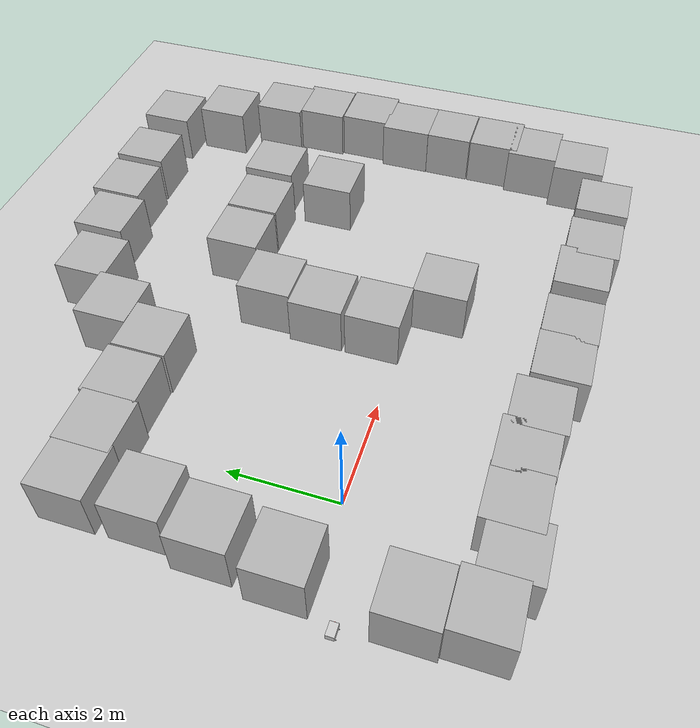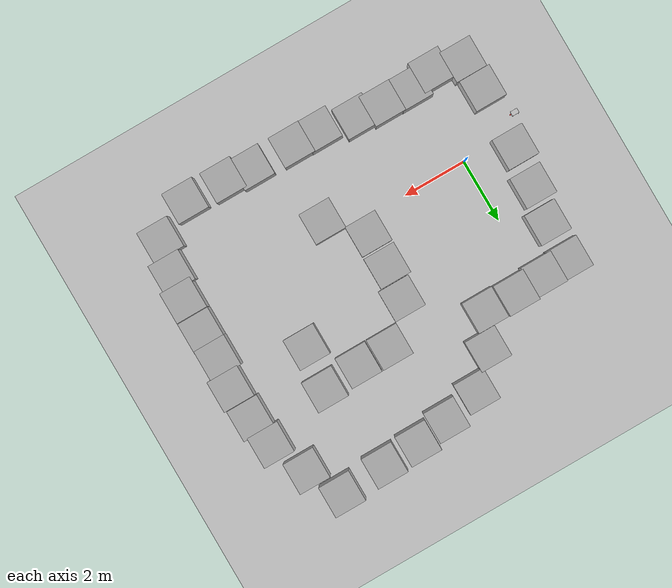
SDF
<?xml version="1.0"?>
<sdf version="1.6">
  <world name="default">

    <plugin
      filename="gz-sim-physics-system"
      name="gz::sim::systems::Physics">
    </plugin>
    <plugin
      filename="gz-sim-user-commands-system"
      name="gz::sim::systems::UserCommands">
    </plugin>
    <plugin
      filename="gz-sim-scene-broadcaster-system"
      name="gz::sim::systems::SceneBroadcaster">
    </plugin>
    <plugin
      filename="gz-sim-sensors-system"
      name="gz::sim::systems::Sensors">
      <render_engine>ogre2</render_engine>
    </plugin>
    <plugin
      filename="gz-sim-imu-system"
      name="gz::sim::systems::Imu">
    </plugin>
    <include>
      <uri>
        https://fuel.gazebosim.org/1.0/OpenRobotics/models/Ground Plane
      </uri>
    </include>

    <include>
      <uri>
        https://fuel.gazebosim.org/1.0/OpenRobotics/models/Sun
      </uri>
    </include>
    <gui fullscreen='0'>
      <camera name='user_camera'>
        <pose frame=''>0.319654 -0.235002 9.29441 0 1.5138 0.009599</pose>
        <view_controller>orbit</view_controller>
        <projection_type>perspective</projection_type>
      </camera>
      <plugin filename="MinimalScene" name="3D View">
        <gz-gui>
          <title>3D View</title>
          <property type="bool" key="showTitleBar">false</property>
          <property type="string" key="state">docked</property>
        </gz-gui>

        <engine>ogre2</engine>
        <scene>scene</scene>
        <ambient_light>0.4 0.4 0.4</ambient_light>
        <background_color>0.8 0.8 0.8</background_color>
        <camera_pose>0.319654 -0.235002 9.29441 0 1.5138 0.009599</camera_pose>
      </plugin>

      <plugin filename="EntityContextMenuPlugin" name="Entity context menu">
        <gz-gui>
          <property key="state" type="string">floating</property>
          <property key="width" type="double">5</property>
          <property key="height" type="double">5</property>
          <property key="showTitleBar" type="bool">false</property>
        </gz-gui>
      </plugin>
      <plugin filename="GzSceneManager" name="Scene Manager">
        <gz-gui>
          <property key="resizable" type="bool">false</property>
          <property key="width" type="double">5</property>
          <property key="height" type="double">5</property>
          <property key="state" type="string">floating</property>
          <property key="showTitleBar" type="bool">false</property>
        </gz-gui>
      </plugin>
      <plugin filename="InteractiveViewControl" name="Interactive view control">
        <gz-gui>
          <property key="resizable" type="bool">false</property>
          <property key="width" type="double">5</property>
          <property key="height" type="double">5</property>
          <property key="state" type="string">floating</property>
          <property key="showTitleBar" type="bool">false</property>
        </gz-gui>
      </plugin>
      <plugin filename="CameraTracking" name="Camera Tracking">
        <gz-gui>
          <property key="resizable" type="bool">false</property>
          <property key="width" type="double">5</property>
          <property key="height" type="double">5</property>
          <property key="state" type="string">floating</property>
          <property key="showTitleBar" type="bool">false</property>
        </gz-gui>
      </plugin>
      <plugin filename="MarkerManager" name="Marker manager">
        <gz-gui>
          <property key="resizable" type="bool">false</property>
          <property key="width" type="double">5</property>
          <property key="height" type="double">5</property>
          <property key="state" type="string">floating</property>
          <property key="showTitleBar" type="bool">false</property>
        </gz-gui>
      </plugin>
      <plugin filename="SelectEntities" name="Select Entities">
        <gz-gui>
          <property key="resizable" type="bool">false</property>
          <property key="width" type="double">5</property>
          <property key="height" type="double">5</property>
          <property key="state" type="string">floating</property>
          <property key="showTitleBar" type="bool">false</property>
        </gz-gui>
      </plugin>

      <plugin filename="Spawn" name="Spawn Entities">
        <gz-gui>
          <property key="resizable" type="bool">false</property>
          <property key="width" type="double">5</property>
          <property key="height" type="double">5</property>
          <property key="state" type="string">floating</property>
          <property key="showTitleBar" type="bool">false</property>
        </gz-gui>
      </plugin>

      <plugin filename="VisualizationCapabilities" name="Visualization Capabilities">
        <gz-gui>
          <property key="resizable" type="bool">false</property>
          <property key="width" type="double">5</property>
          <property key="height" type="double">5</property>
          <property key="state" type="string">floating</property>
          <property key="showTitleBar" type="bool">false</property>
        </gz-gui>
      </plugin>

      <!-- World control -->
      <plugin filename="WorldControl" name="World control">
        <gz-gui>
          <title>World control</title>
          <property type="bool" key="showTitleBar">false</property>
          <property type="bool" key="resizable">false</property>
          <property type="double" key="height">72</property>
          <property type="double" key="z">1</property>

          <property type="string" key="state">floating</property>
          <anchors target="3D View">
            <line own="left" target="left"/>
            <line own="bottom" target="bottom"/>
          </anchors>
        </gz-gui>

        <play_pause>true</play_pause>
        <step>true</step>
        <start_paused>true</start_paused>
        <use_event>true</use_event>

      </plugin>

      <!-- World statistics -->
      <plugin filename="WorldStats" name="World stats">
        <gz-gui>
          <title>World stats</title>
          <property type="bool" key="showTitleBar">false</property>
          <property type="bool" key="resizable">false</property>
          <property type="double" key="height">110</property>
          <property type="double" key="width">290</property>
          <property type="double" key="z">1</property>

          <property type="string" key="state">floating</property>
          <anchors target="3D View">
            <line own="right" target="right"/>
            <line own="bottom" target="bottom"/>
          </anchors>
        </gz-gui>

        <sim_time>true</sim_time>
        <real_time>true</real_time>
        <real_time_factor>true</real_time_factor>
        <iterations>true</iterations>
      </plugin>

      <!-- Insert simple shapes -->
      <plugin filename="Shapes" name="Shapes">
        <gz-gui>
          <property key="resizable" type="bool">false</property>
          <property key="x" type="double">0</property>
          <property key="y" type="double">0</property>
          <property key="width" type="double">250</property>
          <property key="height" type="double">50</property>
          <property key="state" type="string">floating</property>
          <property key="showTitleBar" type="bool">false</property>
          <property key="cardBackground" type="string">#666666</property>
        </gz-gui>
      </plugin>

      <!-- Insert lights -->
      <plugin filename="Lights" name="Lights">
        <gz-gui>
          <property key="resizable" type="bool">false</property>
          <property key="x" type="double">250</property>
          <property key="y" type="double">0</property>
          <property key="width" type="double">150</property>
          <property key="height" type="double">50</property>
          <property key="state" type="string">floating</property>
          <property key="showTitleBar" type="bool">false</property>
          <property key="cardBackground" type="string">#666666</property>
        </gz-gui>
      </plugin>

      <!-- Translate / rotate -->
      <plugin filename="TransformControl" name="Transform control">
        <gz-gui>
          <property key="resizable" type="bool">false</property>
          <property key="x" type="double">0</property>
          <property key="y" type="double">50</property>
          <property key="width" type="double">250</property>
          <property key="height" type="double">50</property>
          <property key="state" type="string">floating</property>
          <property key="showTitleBar" type="bool">false</property>
          <property key="cardBackground" type="string">#777777</property>
        </gz-gui>
      </plugin>

      <!-- Screenshot -->
      <plugin filename="Screenshot" name="Screenshot">
        <gz-gui>
          <property key="resizable" type="bool">false</property>
          <property key="x" type="double">250</property>
          <property key="y" type="double">50</property>
          <property key="width" type="double">50</property>
          <property key="height" type="double">50</property>
          <property key="state" type="string">floating</property>
          <property key="showTitleBar" type="bool">false</property>
          <property key="cardBackground" type="string">#777777</property>
        </gz-gui>
      </plugin>

      <!-- Copy/Paste -->
      <plugin filename="CopyPaste" name="CopyPaste">
        <gz-gui>
          <property key="resizable" type="bool">false</property>
          <property key="x" type="double">300</property>
          <property key="y" type="double">50</property>
          <property key="width" type="double">100</property>
          <property key="height" type="double">50</property>
          <property key="state" type="string">floating</property>
          <property key="showTitleBar" type="bool">false</property>
          <property key="cardBackground" type="string">#777777</property>
        </gz-gui>
      </plugin>

      <!-- Inspector -->
      <plugin filename="ComponentInspector" name="Component inspector">
        <gz-gui>
          <property type="bool" key="showTitleBar">false</property>
          <property type="string" key="state">docked</property>
        </gz-gui>
      </plugin>

      <!-- Entity tree -->
      <plugin filename="EntityTree" name="Entity tree">
        <gz-gui>
          <property type="bool" key="showTitleBar">false</property>
          <property type="string" key="state">docked</property>
        </gz-gui>
      </plugin>
    </gui>

    <physics type="ode">
      <real_time_update_rate>1000.0</real_time_update_rate>
      <max_step_size>0.001</max_step_size>
      <real_time_factor>1</real_time_factor>
      <ode>
        <solver>
          <type>quick</type>
          <iters>150</iters>
          <precon_iters>0</precon_iters>
          <sor>1.400000</sor>
          <use_dynamic_moi_rescaling>1</use_dynamic_moi_rescaling>
        </solver>
        <constraints>
          <cfm>0.00001</cfm>
          <erp>0.2</erp>
          <contact_max_correcting_vel>2000.000000</contact_max_correcting_vel>
          <contact_surface_layer>0.01000</contact_surface_layer>
        </constraints>
      </ode>
    </physics>

    <model name='box'>
      <pose>3.6079806462820692 2.5253344699081568 0.5 0 0 0</pose>
      <link name='box_link'>
        <inertial>
          <inertia>
            <ixx>0.16666</ixx>
            <ixy>0</ixy>
            <ixz>0</ixz>
            <iyy>0.16666</iyy>
            <iyz>0</iyz>
            <izz>0.16666</izz>
          </inertia>
          <mass>1</mass>
          <pose>0 0 0 0 0 0</pose>
        </inertial>
        <collision name='box_collision'>
          <geometry>
            <box>
              <size>1 1 1</size>
            </box>
          </geometry>
          <surface>
            <friction>
              <ode/>
            </friction>
            <bounce/>
            <contact/>
          </surface>
        </collision>
        <visual name='box_visual'>
          <geometry>
            <box>
              <size>1 1 1</size>
            </box>
          </geometry>
          <material>
            <ambient>0.300000012 0.300000012 0.300000012 1</ambient>
            <diffuse>0.699999988 0.699999988 0.699999988 1</diffuse>
            <specular>1 1 1 1</specular>
          </material>
        </visual>
        <pose>0 0 0 0 0 0</pose>
        <enable_wind>false</enable_wind>
      </link>
      <static>false</static>
      <self_collide>false</self_collide>
    </model>
    <model name='box_0'>
      <pose>3.494922661512998 1.4978176082880186 0.5 0 0 0</pose>
      <link name='box_link'>
        <inertial>
          <inertia>
            <ixx>0.16666</ixx>
            <ixy>0</ixy>
            <ixz>0</ixz>
            <iyy>0.16666</iyy>
            <iyz>0</iyz>
            <izz>0.16666</izz>
          </inertia>
          <mass>1</mass>
          <pose>0 0 0 0 0 0</pose>
        </inertial>
        <collision name='box_collision'>
          <geometry>
            <box>
              <size>1 1 1</size>
            </box>
          </geometry>
          <surface>
            <friction>
              <ode/>
            </friction>
            <bounce/>
            <contact/>
          </surface>
        </collision>
        <visual name='box_visual'>
          <geometry>
            <box>
              <size>1 1 1</size>
            </box>
          </geometry>
          <material>
            <ambient>0.300000012 0.300000012 0.300000012 1</ambient>
            <diffuse>0.699999988 0.699999988 0.699999988 1</diffuse>
            <specular>1 1 1 1</specular>
          </material>
        </visual>
        <pose>0 0 0 0 0 0</pose>
        <enable_wind>false</enable_wind>
      </link>
      <static>false</static>
      <self_collide>false</self_collide>
    </model>
    <model name='box_1'>
      <pose>3.4949225119613967 0.43225630653054864 0.5 0 0 0</pose>
      <link name='box_link'>
        <inertial>
          <inertia>
            <ixx>0.16666</ixx>
            <ixy>0</ixy>
            <ixz>0</ixz>
            <iyy>0.16666</iyy>
            <iyz>0</iyz>
            <izz>0.16666</izz>
          </inertia>
          <mass>1</mass>
          <pose>0 0 0 0 0 0</pose>
        </inertial>
        <collision name='box_collision'>
          <geometry>
            <box>
              <size>1 1 1</size>
            </box>
          </geometry>
          <surface>
            <friction>
              <ode/>
            </friction>
            <bounce/>
            <contact/>
          </surface>
        </collision>
        <visual name='box_visual'>
          <geometry>
            <box>
              <size>1 1 1</size>
            </box>
          </geometry>
          <material>
            <ambient>0.300000012 0.300000012 0.300000012 1</ambient>
            <diffuse>0.699999988 0.699999988 0.699999988 1</diffuse>
            <specular>1 1 1 1</specular>
          </material>
        </visual>
        <pose>0 0 0 0 0 0</pose>
        <enable_wind>false</enable_wind>
      </link>
      <static>false</static>
      <self_collide>false</self_collide>
    </model>
    <model name='box_2'>
      <pose>4.4630594434975066 -0.55153767207256765 0.5 0 0 0</pose>
      <link name='box_link'>
        <inertial>
          <inertia>
            <ixx>0.16666</ixx>
            <ixy>0</ixy>
            <ixz>0</ixz>
            <iyy>0.16666</iyy>
            <iyz>0</iyz>
            <izz>0.16666</izz>
          </inertia>
          <mass>1</mass>
          <pose>0 0 0 0 0 0</pose>
        </inertial>
        <collision name='box_collision'>
          <geometry>
            <box>
              <size>1 1 1</size>
            </box>
          </geometry>
          <surface>
            <friction>
              <ode/>
            </friction>
            <bounce/>
            <contact/>
          </surface>
        </collision>
        <visual name='box_visual'>
          <geometry>
            <box>
              <size>1 1 1</size>
            </box>
          </geometry>
          <material>
            <ambient>0.300000012 0.300000012 0.300000012 1</ambient>
            <diffuse>0.699999988 0.699999988 0.699999988 1</diffuse>
            <specular>1 1 1 1</specular>
          </material>
        </visual>
        <pose>0 0 0 0 0 0</pose>
        <enable_wind>false</enable_wind>
      </link>
      <static>false</static>
      <self_collide>false</self_collide>
    </model>
    <model name='box_3'>
      <pose>4.6129606843978133 3.5565113103014911 0.5 0 0 0</pose>
      <link name='box_link'>
        <inertial>
          <inertia>
            <ixx>0.16666</ixx>
            <ixy>0</ixy>
            <ixz>0</ixz>
            <iyy>0.16666</iyy>
            <iyz>0</iyz>
            <izz>0.16666</izz>
          </inertia>
          <mass>1</mass>
          <pose>0 0 0 0 0 0</pose>
        </inertial>
        <collision name='box_collision'>
          <geometry>
            <box>
              <size>1 1 1</size>
            </box>
          </geometry>
          <surface>
            <friction>
              <ode/>
            </friction>
            <bounce/>
            <contact/>
          </surface>
        </collision>
        <visual name='box_visual'>
          <geometry>
            <box>
              <size>1 1 1</size>
            </box>
          </geometry>
          <material>
            <ambient>0.300000012 0.300000012 0.300000012 1</ambient>
            <diffuse>0.699999988 0.699999988 0.699999988 1</diffuse>
            <specular>1 1 1 1</specular>
          </material>
        </visual>
        <pose>0 0 0 0 0 0</pose>
        <enable_wind>false</enable_wind>
      </link>
      <static>false</static>
      <self_collide>false</self_collide>
    </model>
    <model name='box_4'>
      <pose>1.7010573270226828 4.030552841706303 0.5 0 0 0</pose>
      <link name='box_link'>
        <inertial>
          <inertia>
            <ixx>0.16666</ixx>
            <ixy>0</ixy>
            <ixz>0</ixz>
            <iyy>0.16666</iyy>
            <iyz>0</iyz>
            <izz>0.16666</izz>
          </inertia>
          <mass>1</mass>
          <pose>0 0 0 0 0 0</pose>
        </inertial>
        <collision name='box_collision'>
          <geometry>
            <box>
              <size>1 1 1</size>
            </box>
          </geometry>
          <surface>
            <friction>
              <ode/>
            </friction>
            <bounce/>
            <contact/>
          </surface>
        </collision>
        <visual name='box_visual'>
          <geometry>
            <box>
              <size>1 1 1</size>
            </box>
          </geometry>
          <material>
            <ambient>0.300000012 0.300000012 0.300000012 1</ambient>
            <diffuse>0.699999988 0.699999988 0.699999988 1</diffuse>
            <specular>1 1 1 1</specular>
          </material>
        </visual>
        <pose>0 0 0 0 0 0</pose>
        <enable_wind>false</enable_wind>
      </link>
      <static>false</static>
      <self_collide>false</self_collide>
    </model>
    <model name='box_5'>
      <pose>1.2582054842673047 -2.6145004932012856 0.5 0 0 0</pose>
      <link name='box_link'>
        <inertial>
          <inertia>
            <ixx>0.16666</ixx>
            <ixy>0</ixy>
            <ixz>0</ixz>
            <iyy>0.16666</iyy>
            <iyz>0</iyz>
            <izz>0.16666</izz>
          </inertia>
          <mass>1</mass>
          <pose>0 0 0 0 0 0</pose>
        </inertial>
        <collision name='box_collision'>
          <geometry>
            <box>
              <size>1 1 1</size>
            </box>
          </geometry>
          <surface>
            <friction>
              <ode/>
            </friction>
            <bounce/>
            <contact/>
          </surface>
        </collision>
        <visual name='box_visual'>
          <geometry>
            <box>
              <size>1 1 1</size>
            </box>
          </geometry>
          <material>
            <ambient>0.300000012 0.300000012 0.300000012 1</ambient>
            <diffuse>0.699999988 0.699999988 0.699999988 1</diffuse>
            <specular>1 1 1 1</specular>
          </material>
        </visual>
        <pose>0 0 0 0 0 0</pose>
        <enable_wind>false</enable_wind>
      </link>
      <static>false</static>
      <self_collide>false</self_collide>
    </model>
    <model name='box_6'>
      <pose>0.6706154942855127 4.0535003850697073 0.5 0 0 0</pose>
      <link name='box_link'>
        <inertial>
          <inertia>
            <ixx>0.16666</ixx>
            <ixy>0</ixy>
            <ixz>0</ixz>
            <iyy>0.16666</iyy>
            <iyz>0</iyz>
            <izz>0.16666</izz>
          </inertia>
          <mass>1</mass>
          <pose>0 0 0 0 0 0</pose>
        </inertial>
        <collision name='box_collision'>
          <geometry>
            <box>
              <size>1 1 1</size>
            </box>
          </geometry>
          <surface>
            <friction>
              <ode/>
            </friction>
            <bounce/>
            <contact/>
          </surface>
        </collision>
        <visual name='box_visual'>
          <geometry>
            <box>
              <size>1 1 1</size>
            </box>
          </geometry>
          <material>
            <ambient>0.300000012 0.300000012 0.300000012 1</ambient>
            <diffuse>0.699999988 0.699999988 0.699999988 1</diffuse>
            <specular>1 1 1 1</specular>
          </material>
        </visual>
        <pose>0 0 0 0 0 0</pose>
        <enable_wind>false</enable_wind>
      </link>
      <static>false</static>
      <self_collide>false</self_collide>
    </model>
    <model name='box_7'>
      <pose>-0.28243669711069896 3.998690358394934 0.5 0 0 0</pose>
      <link name='box_link'>
        <inertial>
          <inertia>
            <ixx>0.16666</ixx>
            <ixy>0</ixy>
            <ixz>0</ixz>
            <iyy>0.16666</iyy>
            <iyz>0</iyz>
            <izz>0.16666</izz>
          </inertia>
          <mass>1</mass>
          <pose>0 0 0 0 0 0</pose>
        </inertial>
        <collision name='box_collision'>
          <geometry>
            <box>
              <size>1 1 1</size>
            </box>
          </geometry>
          <surface>
            <friction>
              <ode/>
            </friction>
            <bounce/>
            <contact/>
          </surface>
        </collision>
        <visual name='box_visual'>
          <geometry>
            <box>
              <size>1 1 1</size>
            </box>
          </geometry>
          <material>
            <ambient>0.300000012 0.300000012 0.300000012 1</ambient>
            <diffuse>0.699999988 0.699999988 0.699999988 1</diffuse>
            <specular>1 1 1 1</specular>
          </material>
        </visual>
        <pose>0 0 0 0 0 0</pose>
        <enable_wind>false</enable_wind>
      </link>
      <static>false</static>
      <self_collide>false</self_collide>
    </model>
    <model name='box_8'>
      <pose>2.1924004107482391 5.0349059945521963 0.5 0 0 0</pose>
      <link name='box_link'>
        <inertial>
          <inertia>
            <ixx>0.16666</ixx>
            <ixy>0</ixy>
            <ixz>0</ixz>
            <iyy>0.16666</iyy>
            <iyz>0</iyz>
            <izz>0.16666</izz>
          </inertia>
          <mass>1</mass>
          <pose>0 0 0 0 0 0</pose>
        </inertial>
        <collision name='box_collision'>
          <geometry>
            <box>
              <size>1 1 1</size>
            </box>
          </geometry>
          <surface>
            <friction>
              <ode/>
            </friction>
            <bounce/>
            <contact/>
          </surface>
        </collision>
        <visual name='box_visual'>
          <geometry>
            <box>
              <size>1 1 1</size>
            </box>
          </geometry>
          <material>
            <ambient>0.300000012 0.300000012 0.300000012 1</ambient>
            <diffuse>0.699999988 0.699999988 0.699999988 1</diffuse>
            <specular>1 1 1 1</specular>
          </material>
        </visual>
        <pose>0 0 0 0 0 0</pose>
        <enable_wind>false</enable_wind>
      </link>
      <static>false</static>
      <self_collide>false</self_collide>
    </model>
    <model name='box_9'>
      <pose>3.0943881696765345 5.935421168770171 0.5 0 0 0</pose>
      <link name='box_link'>
        <inertial>
          <inertia>
            <ixx>0.16666</ixx>
            <ixy>0</ixy>
            <ixz>0</ixz>
            <iyy>0.16666</iyy>
            <iyz>0</iyz>
            <izz>0.16666</izz>
          </inertia>
          <mass>1</mass>
          <pose>0 0 0 0 0 0</pose>
        </inertial>
        <collision name='box_collision'>
          <geometry>
            <box>
              <size>1 1 1</size>
            </box>
          </geometry>
          <surface>
            <friction>
              <ode/>
            </friction>
            <bounce/>
            <contact/>
          </surface>
        </collision>
        <visual name='box_visual'>
          <geometry>
            <box>
              <size>1 1 1</size>
            </box>
          </geometry>
          <material>
            <ambient>0.300000012 0.300000012 0.300000012 1</ambient>
            <diffuse>0.699999988 0.699999988 0.699999988 1</diffuse>
            <specular>1 1 1 1</specular>
          </material>
        </visual>
        <pose>0 0 0 0 0 0</pose>
        <enable_wind>false</enable_wind>
      </link>
      <static>false</static>
      <self_collide>false</self_collide>
    </model>
    <model name='box_10'>
      <pose>4.2585700037728076 6.2045571536851858 0.5 0 0 0</pose>
      <link name='box_link'>
        <inertial>
          <inertia>
            <ixx>0.16666</ixx>
            <ixy>0</ixy>
            <ixz>0</ixz>
            <iyy>0.16666</iyy>
            <iyz>0</iyz>
            <izz>0.16666</izz>
          </inertia>
          <mass>1</mass>
          <pose>0 0 0 0 0 0</pose>
        </inertial>
        <collision name='box_collision'>
          <geometry>
            <box>
              <size>1 1 1</size>
            </box>
          </geometry>
          <surface>
            <friction>
              <ode/>
            </friction>
            <bounce/>
            <contact/>
          </surface>
        </collision>
        <visual name='box_visual'>
          <geometry>
            <box>
              <size>1 1 1</size>
            </box>
          </geometry>
          <material>
            <ambient>0.300000012 0.300000012 0.300000012 1</ambient>
            <diffuse>0.699999988 0.699999988 0.699999988 1</diffuse>
            <specular>1 1 1 1</specular>
          </material>
        </visual>
        <pose>0 0 0 0 0 0</pose>
        <enable_wind>false</enable_wind>
      </link>
      <static>false</static>
      <self_collide>false</self_collide>
    </model>
    <model name='box_11'>
      <pose>5.3105900201871208 6.3755920427107595 0.5 0 0 0</pose>
      <link name='box_link'>
        <inertial>
          <inertia>
            <ixx>0.16666</ixx>
            <ixy>0</ixy>
            <ixz>0</ixz>
            <iyy>0.16666</iyy>
            <iyz>0</iyz>
            <izz>0.16666</izz>
          </inertia>
          <mass>1</mass>
          <pose>0 0 0 0 0 0</pose>
        </inertial>
        <collision name='box_collision'>
          <geometry>
            <box>
              <size>1 1 1</size>
            </box>
          </geometry>
          <surface>
            <friction>
              <ode/>
            </friction>
            <bounce/>
            <contact/>
          </surface>
        </collision>
        <visual name='box_visual'>
          <geometry>
            <box>
              <size>1 1 1</size>
            </box>
          </geometry>
          <material>
            <ambient>0.300000012 0.300000012 0.300000012 1</ambient>
            <diffuse>0.699999988 0.699999988 0.699999988 1</diffuse>
            <specular>1 1 1 1</specular>
          </material>
        </visual>
        <pose>0 0 0 0 0 0</pose>
        <enable_wind>false</enable_wind>
      </link>
      <static>false</static>
      <self_collide>false</self_collide>
    </model>
    <model name='box_12'>
      <pose>5.6576209379890132 3.5563111186137712 0.5 0 0 0</pose>
      <link name='box_link'>
        <inertial>
          <inertia>
            <ixx>0.16666</ixx>
            <ixy>0</ixy>
            <ixz>0</ixz>
            <iyy>0.16666</iyy>
            <iyz>0</iyz>
            <izz>0.16666</izz>
          </inertia>
          <mass>1</mass>
          <pose>0 0 0 0 0 0</pose>
        </inertial>
        <collision name='box_collision'>
          <geometry>
            <box>
              <size>1 1 1</size>
            </box>
          </geometry>
          <surface>
            <friction>
              <ode/>
            </friction>
            <bounce/>
            <contact/>
          </surface>
        </collision>
        <visual name='box_visual'>
          <geometry>
            <box>
              <size>1 1 1</size>
            </box>
          </geometry>
          <material>
            <ambient>0.300000012 0.300000012 0.300000012 1</ambient>
            <diffuse>0.699999988 0.699999988 0.699999988 1</diffuse>
            <specular>1 1 1 1</specular>
          </material>
        </visual>
        <pose>0 0 0 0 0 0</pose>
        <enable_wind>false</enable_wind>
      </link>
      <static>false</static>
      <self_collide>false</self_collide>
    </model>
    <model name='box_13'>
      <pose>6.8445238250185234 3.6716367676928829 0.5 0 0 0</pose>
      <link name='box_link'>
        <inertial>
          <inertia>
            <ixx>0.16666</ixx>
            <ixy>0</ixy>
            <ixz>0</ixz>
            <iyy>0.16666</iyy>
            <iyz>0</iyz>
            <izz>0.16666</izz>
          </inertia>
          <mass>1</mass>
          <pose>0 0 0 0 0 0</pose>
        </inertial>
        <collision name='box_collision'>
          <geometry>
            <box>
              <size>1 1 1</size>
            </box>
          </geometry>
          <surface>
            <friction>
              <ode/>
            </friction>
            <bounce/>
            <contact/>
          </surface>
        </collision>
        <visual name='box_visual'>
          <geometry>
            <box>
              <size>1 1 1</size>
            </box>
          </geometry>
          <material>
            <ambient>0.300000012 0.300000012 0.300000012 1</ambient>
            <diffuse>0.699999988 0.699999988 0.699999988 1</diffuse>
            <specular>1 1 1 1</specular>
          </material>
        </visual>
        <pose>0 0 0 0 0 0</pose>
        <enable_wind>false</enable_wind>
      </link>
      <static>false</static>
      <self_collide>false</self_collide>
    </model>
    <model name='box_14'>
      <pose>6.6850749643542642 2.3500961326875913 0.5 0 0 0</pose>
      <link name='box_link'>
        <inertial>
          <inertia>
            <ixx>0.16666</ixx>
            <ixy>0</ixy>
            <ixz>0</ixz>
            <iyy>0.16666</iyy>
            <iyz>0</iyz>
            <izz>0.16666</izz>
          </inertia>
          <mass>1</mass>
          <pose>0 0 0 0 0 0</pose>
        </inertial>
        <collision name='box_collision'>
          <geometry>
            <box>
              <size>1 1 1</size>
            </box>
          </geometry>
          <surface>
            <friction>
              <ode/>
            </friction>
            <bounce/>
            <contact/>
          </surface>
        </collision>
        <visual name='box_visual'>
          <geometry>
            <box>
              <size>1 1 1</size>
            </box>
          </geometry>
          <material>
            <ambient>0.300000012 0.300000012 0.300000012 1</ambient>
            <diffuse>0.699999988 0.699999988 0.699999988 1</diffuse>
            <specular>1 1 1 1</specular>
          </material>
        </visual>
        <pose>0 0 0 0 0 0</pose>
        <enable_wind>false</enable_wind>
      </link>
      <static>false</static>
      <self_collide>false</self_collide>
    </model>
    <model name='box_15'>
      <pose>6.4658853912472667 6.4337428037039084 0.5 0 0 0</pose>
      <link name='box_link'>
        <inertial>
          <inertia>
            <ixx>0.16666</ixx>
            <ixy>0</ixy>
            <ixz>0</ixz>
            <iyy>0.16666</iyy>
            <iyz>0</iyz>
            <izz>0.16666</izz>
          </inertia>
          <mass>1</mass>
          <pose>0 0 0 0 0 0</pose>
        </inertial>
        <collision name='box_collision'>
          <geometry>
            <box>
              <size>1 1 1</size>
            </box>
          </geometry>
          <surface>
            <friction>
              <ode/>
            </friction>
            <bounce/>
            <contact/>
          </surface>
        </collision>
        <visual name='box_visual'>
          <geometry>
            <box>
              <size>1 1 1</size>
            </box>
          </geometry>
          <material>
            <ambient>0.300000012 0.300000012 0.300000012 1</ambient>
            <diffuse>0.699999988 0.699999988 0.699999988 1</diffuse>
            <specular>1 1 1 1</specular>
          </material>
        </visual>
        <pose>0 0 0 0 0 0</pose>
        <enable_wind>false</enable_wind>
      </link>
      <static>false</static>
      <self_collide>false</self_collide>
    </model>
    <model name='box_16'>
      <pose>7.9377326440930922 6.5307673034264573 0.5 0 0 0</pose>
      <link name='box_link'>
        <inertial>
          <inertia>
            <ixx>0.16666</ixx>
            <ixy>0</ixy>
            <ixz>0</ixz>
            <iyy>0.16666</iyy>
            <iyz>0</iyz>
            <izz>0.16666</izz>
          </inertia>
          <mass>1</mass>
          <pose>0 0 0 0 0 0</pose>
        </inertial>
        <collision name='box_collision'>
          <geometry>
            <box>
              <size>1 1 1</size>
            </box>
          </geometry>
          <surface>
            <friction>
              <ode/>
            </friction>
            <bounce/>
            <contact/>
          </surface>
        </collision>
        <visual name='box_visual'>
          <geometry>
            <box>
              <size>1 1 1</size>
            </box>
          </geometry>
          <material>
            <ambient>0.300000012 0.300000012 0.300000012 1</ambient>
            <diffuse>0.699999988 0.699999988 0.699999988 1</diffuse>
            <specular>1 1 1 1</specular>
          </material>
        </visual>
        <pose>0 0 0 0 0 0</pose>
        <enable_wind>false</enable_wind>
      </link>
      <static>false</static>
      <self_collide>false</self_collide>
    </model>
    <model name='box_17'>
      <pose>8.489075274650741 5.4324560446104639 0.5 0 0 0</pose>
      <link name='box_link'>
        <inertial>
          <inertia>
            <ixx>0.16666</ixx>
            <ixy>0</ixy>
            <ixz>0</ixz>
            <iyy>0.16666</iyy>
            <iyz>0</iyz>
            <izz>0.16666</izz>
          </inertia>
          <mass>1</mass>
          <pose>0 0 0 0 0 0</pose>
        </inertial>
        <collision name='box_collision'>
          <geometry>
            <box>
              <size>1 1 1</size>
            </box>
          </geometry>
          <surface>
            <friction>
              <ode/>
            </friction>
            <bounce/>
            <contact/>
          </surface>
        </collision>
        <visual name='box_visual'>
          <geometry>
            <box>
              <size>1 1 1</size>
            </box>
          </geometry>
          <material>
            <ambient>0.300000012 0.300000012 0.300000012 1</ambient>
            <diffuse>0.699999988 0.699999988 0.699999988 1</diffuse>
            <specular>1 1 1 1</specular>
          </material>
        </visual>
        <pose>0 0 0 0 0 0</pose>
        <enable_wind>false</enable_wind>
      </link>
      <static>false</static>
      <self_collide>false</self_collide>
    </model>
    <model name='box_18'>
      <pose>8.9993868971396527 4.2652200928359667 0.5 0 0 0</pose>
      <link name='box_link'>
        <inertial>
          <inertia>
            <ixx>0.16666</ixx>
            <ixy>0</ixy>
            <ixz>0</ixz>
            <iyy>0.16666</iyy>
            <iyz>0</iyz>
            <izz>0.16666</izz>
          </inertia>
          <mass>1</mass>
          <pose>0 0 0 0 0 0</pose>
        </inertial>
        <collision name='box_collision'>
          <geometry>
            <box>
              <size>1 1 1</size>
            </box>
          </geometry>
          <surface>
            <friction>
              <ode/>
            </friction>
            <bounce/>
            <contact/>
          </surface>
        </collision>
        <visual name='box_visual'>
          <geometry>
            <box>
              <size>1 1 1</size>
            </box>
          </geometry>
          <material>
            <ambient>0.300000012 0.300000012 0.300000012 1</ambient>
            <diffuse>0.699999988 0.699999988 0.699999988 1</diffuse>
            <specular>1 1 1 1</specular>
          </material>
        </visual>
        <pose>0 0 0 0 0 0</pose>
        <enable_wind>false</enable_wind>
      </link>
      <static>false</static>
      <self_collide>false</self_collide>
    </model>
    <model name='box_19'>
      <pose>9.1200137525792453 3.3051426735149634 0.5 0 0 0</pose>
      <link name='box_link'>
        <inertial>
          <inertia>
            <ixx>0.16666</ixx>
            <ixy>0</ixy>
            <ixz>0</ixz>
            <iyy>0.16666</iyy>
            <iyz>0</iyz>
            <izz>0.16666</izz>
          </inertia>
          <mass>1</mass>
          <pose>0 0 0 0 0 0</pose>
        </inertial>
        <collision name='box_collision'>
          <geometry>
            <box>
              <size>1 1 1</size>
            </box>
          </geometry>
          <surface>
            <friction>
              <ode/>
            </friction>
            <bounce/>
            <contact/>
          </surface>
        </collision>
        <visual name='box_visual'>
          <geometry>
            <box>
              <size>1 1 1</size>
            </box>
          </geometry>
          <material>
            <ambient>0.300000012 0.300000012 0.300000012 1</ambient>
            <diffuse>0.699999988 0.699999988 0.699999988 1</diffuse>
            <specular>1 1 1 1</specular>
          </material>
        </visual>
        <pose>0 0 0 0 0 0</pose>
        <enable_wind>false</enable_wind>
      </link>
      <static>false</static>
      <self_collide>false</self_collide>
    </model>
    <model name='box_20'>
      <pose>9.1841314681459441 2.2883809486798574 0.5 0 0 0</pose>
      <link name='box_link'>
        <inertial>
          <inertia>
            <ixx>0.16666</ixx>
            <ixy>0</ixy>
            <ixz>0</ixz>
            <iyy>0.16666</iyy>
            <iyz>0</iyz>
            <izz>0.16666</izz>
          </inertia>
          <mass>1</mass>
          <pose>0 0 0 0 0 0</pose>
        </inertial>
        <collision name='box_collision'>
          <geometry>
            <box>
              <size>1 1 1</size>
            </box>
          </geometry>
          <surface>
            <friction>
              <ode/>
            </friction>
            <bounce/>
            <contact/>
          </surface>
        </collision>
        <visual name='box_visual'>
          <geometry>
            <box>
              <size>1 1 1</size>
            </box>
          </geometry>
          <material>
            <ambient>0.300000012 0.300000012 0.300000012 1</ambient>
            <diffuse>0.699999988 0.699999988 0.699999988 1</diffuse>
            <specular>1 1 1 1</specular>
          </material>
        </visual>
        <pose>0 0 0 0 0 0</pose>
        <enable_wind>false</enable_wind>
      </link>
      <static>false</static>
      <self_collide>false</self_collide>
    </model>
    <model name='box_21'>
      <pose>9.063379541916289 1.3298336882098427 0.5 0 0 0</pose>
      <link name='box_link'>
        <inertial>
          <inertia>
            <ixx>0.16666</ixx>
            <ixy>0</ixy>
            <ixz>0</ixz>
            <iyy>0.16666</iyy>
            <iyz>0</iyz>
            <izz>0.16666</izz>
          </inertia>
          <mass>1</mass>
          <pose>0 0 0 0 0 0</pose>
        </inertial>
        <collision name='box_collision'>
          <geometry>
            <box>
              <size>1 1 1</size>
            </box>
          </geometry>
          <surface>
            <friction>
              <ode/>
            </friction>
            <bounce/>
            <contact/>
          </surface>
        </collision>
        <visual name='box_visual'>
          <geometry>
            <box>
              <size>1 1 1</size>
            </box>
          </geometry>
          <material>
            <ambient>0.300000012 0.300000012 0.300000012 1</ambient>
            <diffuse>0.699999988 0.699999988 0.699999988 1</diffuse>
            <specular>1 1 1 1</specular>
          </material>
        </visual>
        <pose>0 0 0 0 0 0</pose>
        <enable_wind>false</enable_wind>
      </link>
      <static>false</static>
      <self_collide>false</self_collide>
    </model>
    <model name='box_22'>
      <pose>9.0692906387283401 0.41422661622399137 0.5 0 0 0</pose>
      <link name='box_link'>
        <inertial>
          <inertia>
            <ixx>0.16666</ixx>
            <ixy>0</ixy>
            <ixz>0</ixz>
            <iyy>0.16666</iyy>
            <iyz>0</iyz>
            <izz>0.16666</izz>
          </inertia>
          <mass>1</mass>
          <pose>0 0 0 0 0 0</pose>
        </inertial>
        <collision name='box_collision'>
          <geometry>
            <box>
              <size>1 1 1</size>
            </box>
          </geometry>
          <surface>
            <friction>
              <ode/>
            </friction>
            <bounce/>
            <contact/>
          </surface>
        </collision>
        <visual name='box_visual'>
          <geometry>
            <box>
              <size>1 1 1</size>
            </box>
          </geometry>
          <material>
            <ambient>0.300000012 0.300000012 0.300000012 1</ambient>
            <diffuse>0.699999988 0.699999988 0.699999988 1</diffuse>
            <specular>1 1 1 1</specular>
          </material>
        </visual>
        <pose>0 0 0 0 0 0</pose>
        <enable_wind>false</enable_wind>
      </link>
      <static>false</static>
      <self_collide>false</self_collide>
    </model>
    <model name='box_23'>
      <pose>9.071077363160498 -0.6060927547291548 0.5 0 0 0</pose>
      <link name='box_link'>
        <inertial>
          <inertia>
            <ixx>0.16666</ixx>
            <ixy>0</ixy>
            <ixz>0</ixz>
            <iyy>0.16666</iyy>
            <iyz>0</iyz>
            <izz>0.16666</izz>
          </inertia>
          <mass>1</mass>
          <pose>0 0 0 0 0 0</pose>
        </inertial>
        <collision name='box_collision'>
          <geometry>
            <box>
              <size>1 1 1</size>
            </box>
          </geometry>
          <surface>
            <friction>
              <ode/>
            </friction>
            <bounce/>
            <contact/>
          </surface>
        </collision>
        <visual name='box_visual'>
          <geometry>
            <box>
              <size>1 1 1</size>
            </box>
          </geometry>
          <material>
            <ambient>0.300000012 0.300000012 0.300000012 1</ambient>
            <diffuse>0.699999988 0.699999988 0.699999988 1</diffuse>
            <specular>1 1 1 1</specular>
          </material>
        </visual>
        <pose>0 0 0 0 0 0</pose>
        <enable_wind>false</enable_wind>
      </link>
      <static>false</static>
      <self_collide>false</self_collide>
    </model>
    <include>
      <uri>model://turtlebot3_burger</uri>
      <name>burger</name>
      <pose>-2 -0.5 0.01 0 0 0</pose>
    </include>
    <model name='box_24'>
      <pose>8.9641439575790862 -1.4589446762157061 0.5 0 0 0</pose>
      <link name='box_link'>
        <inertial>
          <inertia>
            <ixx>0.16666</ixx>
            <ixy>0</ixy>
            <ixz>0</ixz>
            <iyy>0.16666</iyy>
            <iyz>0</iyz>
            <izz>0.16666</izz>
          </inertia>
          <mass>1</mass>
          <pose>0 0 0 0 0 0</pose>
        </inertial>
        <collision name='box_collision'>
          <geometry>
            <box>
              <size>1 1 1</size>
            </box>
          </geometry>
          <surface>
            <friction>
              <ode/>
            </friction>
            <bounce/>
            <contact/>
          </surface>
        </collision>
        <visual name='box_visual'>
          <geometry>
            <box>
              <size>1 1 1</size>
            </box>
          </geometry>
          <material>
            <ambient>0.300000012 0.300000012 0.300000012 1</ambient>
            <diffuse>0.699999988 0.699999988 0.699999988 1</diffuse>
            <specular>1 1 1 1</specular>
          </material>
        </visual>
        <pose>0 0 0 0 0 0</pose>
        <enable_wind>false</enable_wind>
      </link>
      <static>false</static>
      <self_collide>false</self_collide>
    </model>
    <model name='box_25'>
      <pose>8.7633956037249163 -2.4458265250856095 0.5 0 0 0</pose>
      <link name='box_link'>
        <inertial>
          <inertia>
            <ixx>0.16666</ixx>
            <ixy>0</ixy>
            <ixz>0</ixz>
            <iyy>0.16666</iyy>
            <iyz>0</iyz>
            <izz>0.16666</izz>
          </inertia>
          <mass>1</mass>
          <pose>0 0 0 0 0 0</pose>
        </inertial>
        <collision name='box_collision'>
          <geometry>
            <box>
              <size>1 1 1</size>
            </box>
          </geometry>
          <surface>
            <friction>
              <ode/>
            </friction>
            <bounce/>
            <contact/>
          </surface>
        </collision>
        <visual name='box_visual'>
          <geometry>
            <box>
              <size>1 1 1</size>
            </box>
          </geometry>
          <material>
            <ambient>0.300000012 0.300000012 0.300000012 1</ambient>
            <diffuse>0.699999988 0.699999988 0.699999988 1</diffuse>
            <specular>1 1 1 1</specular>
          </material>
        </visual>
        <pose>0 0 0 0 0 0</pose>
        <enable_wind>false</enable_wind>
      </link>
      <static>false</static>
      <self_collide>false</self_collide>
    </model>
    <model name='box_26'>
      <pose>7.579220995664274 -3.0548090183081755 0.5 0 0 0</pose>
      <link name='box_link'>
        <inertial>
          <inertia>
            <ixx>0.16666</ixx>
            <ixy>0</ixy>
            <ixz>0</ixz>
            <iyy>0.16666</iyy>
            <iyz>0</iyz>
            <izz>0.16666</izz>
          </inertia>
          <mass>1</mass>
          <pose>0 0 0 0 0 0</pose>
        </inertial>
        <collision name='box_collision'>
          <geometry>
            <box>
              <size>1 1 1</size>
            </box>
          </geometry>
          <surface>
            <friction>
              <ode/>
            </friction>
            <bounce/>
            <contact/>
          </surface>
        </collision>
        <visual name='box_visual'>
          <geometry>
            <box>
              <size>1 1 1</size>
            </box>
          </geometry>
          <material>
            <ambient>0.300000012 0.300000012 0.300000012 1</ambient>
            <diffuse>0.699999988 0.699999988 0.699999988 1</diffuse>
            <specular>1 1 1 1</specular>
          </material>
        </visual>
        <pose>0 0 0 0 0 0</pose>
        <enable_wind>false</enable_wind>
      </link>
      <static>false</static>
      <self_collide>false</self_collide>
    </model>
    <model name='box_27'>
      <pose>6.3311675806246495 -3.0195628458396437 0.5 0 0 0</pose>
      <link name='box_link'>
        <inertial>
          <inertia>
            <ixx>0.16666</ixx>
            <ixy>0</ixy>
            <ixz>0</ixz>
            <iyy>0.16666</iyy>
            <iyz>0</iyz>
            <izz>0.16666</izz>
          </inertia>
          <mass>1</mass>
          <pose>0 0 0 0 0 0</pose>
        </inertial>
        <collision name='box_collision'>
          <geometry>
            <box>
              <size>1 1 1</size>
            </box>
          </geometry>
          <surface>
            <friction>
              <ode/>
            </friction>
            <bounce/>
            <contact/>
          </surface>
        </collision>
        <visual name='box_visual'>
          <geometry>
            <box>
              <size>1 1 1</size>
            </box>
          </geometry>
          <material>
            <ambient>0.300000012 0.300000012 0.300000012 1</ambient>
            <diffuse>0.699999988 0.699999988 0.699999988 1</diffuse>
            <specular>1 1 1 1</specular>
          </material>
        </visual>
        <pose>0 0 0 0 0 0</pose>
        <enable_wind>false</enable_wind>
      </link>
      <static>false</static>
      <self_collide>false</self_collide>
    </model>
    <model name='box_28'>
      <pose>-1.1457118355510982 3.975423221543966 0.5 0 0 0</pose>
      <link name='box_link'>
        <inertial>
          <inertia>
            <ixx>0.16666</ixx>
            <ixy>0</ixy>
            <ixz>0</ixz>
            <iyy>0.16666</iyy>
            <iyz>0</iyz>
            <izz>0.16666</izz>
          </inertia>
          <mass>1</mass>
          <pose>0 0 0 0 0 0</pose>
        </inertial>
        <collision name='box_collision'>
          <geometry>
            <box>
              <size>1 1 1</size>
            </box>
          </geometry>
          <surface>
            <friction>
              <ode/>
            </friction>
            <bounce/>
            <contact/>
          </surface>
        </collision>
        <visual name='box_visual'>
          <geometry>
            <box>
              <size>1 1 1</size>
            </box>
          </geometry>
          <material>
            <ambient>0.300000012 0.300000012 0.300000012 1</ambient>
            <diffuse>0.699999988 0.699999988 0.699999988 1</diffuse>
            <specular>1 1 1 1</specular>
          </material>
        </visual>
        <pose>0 0 0 0 0 0</pose>
        <enable_wind>false</enable_wind>
      </link>
      <static>false</static>
      <self_collide>false</self_collide>
    </model>
    <model name='box_29'>
      <pose>-1.1316562421509426 2.7544080417719612 0.5 0 0 0</pose>
      <link name='box_link'>
        <inertial>
          <inertia>
            <ixx>0.16666</ixx>
            <ixy>0</ixy>
            <ixz>0</ixz>
            <iyy>0.16666</iyy>
            <iyz>0</iyz>
            <izz>0.16666</izz>
          </inertia>
          <mass>1</mass>
          <pose>0 0 0 0 0 0</pose>
        </inertial>
        <collision name='box_collision'>
          <geometry>
            <box>
              <size>1 1 1</size>
            </box>
          </geometry>
          <surface>
            <friction>
              <ode/>
            </friction>
            <bounce/>
            <contact/>
          </surface>
        </collision>
        <visual name='box_visual'>
          <geometry>
            <box>
              <size>1 1 1</size>
            </box>
          </geometry>
          <material>
            <ambient>0.300000012 0.300000012 0.300000012 1</ambient>
            <diffuse>0.699999988 0.699999988 0.699999988 1</diffuse>
            <specular>1 1 1 1</specular>
          </material>
        </visual>
        <pose>0 0 0 0 0 0</pose>
        <enable_wind>false</enable_wind>
      </link>
      <static>false</static>
      <self_collide>false</self_collide>
    </model>
    <model name='box_30'>
      <pose>-1.3026694518100135 1.6236249406001484 0.5 0 0 0</pose>
      <link name='box_link'>
        <inertial>
          <inertia>
            <ixx>0.16666</ixx>
            <ixy>0</ixy>
            <ixz>0</ixz>
            <iyy>0.16666</iyy>
            <iyz>0</iyz>
            <izz>0.16666</izz>
          </inertia>
          <mass>1</mass>
          <pose>0 0 0 0 0 0</pose>
        </inertial>
        <collision name='box_collision'>
          <geometry>
            <box>
              <size>1 1 1</size>
            </box>
          </geometry>
          <surface>
            <friction>
              <ode/>
            </friction>
            <bounce/>
            <contact/>
          </surface>
        </collision>
        <visual name='box_visual'>
          <geometry>
            <box>
              <size>1 1 1</size>
            </box>
          </geometry>
          <material>
            <ambient>0.300000012 0.300000012 0.300000012 1</ambient>
            <diffuse>0.699999988 0.699999988 0.699999988 1</diffuse>
            <specular>1 1 1 1</specular>
          </material>
        </visual>
        <pose>0 0 0 0 0 0</pose>
        <enable_wind>false</enable_wind>
      </link>
      <static>false</static>
      <self_collide>false</self_collide>
    </model>
    <model name='box_31'>
      <pose>-1.4232277877195247 0.40228871558271467 0.5 0 0 0</pose>
      <link name='box_link'>
        <inertial>
          <inertia>
            <ixx>0.16666</ixx>
            <ixy>0</ixy>
            <ixz>0</ixz>
            <iyy>0.16666</iyy>
            <iyz>0</iyz>
            <izz>0.16666</izz>
          </inertia>
          <mass>1</mass>
          <pose>0 0 0 0 0 0</pose>
        </inertial>
        <collision name='box_collision'>
          <geometry>
            <box>
              <size>1 1 1</size>
            </box>
          </geometry>
          <surface>
            <friction>
              <ode/>
            </friction>
            <bounce/>
            <contact/>
          </surface>
        </collision>
        <visual name='box_visual'>
          <geometry>
            <box>
              <size>1 1 1</size>
            </box>
          </geometry>
          <material>
            <ambient>0.300000012 0.300000012 0.300000012 1</ambient>
            <diffuse>0.699999988 0.699999988 0.699999988 1</diffuse>
            <specular>1 1 1 1</specular>
          </material>
        </visual>
        <pose>0 0 0 0 0 0</pose>
        <enable_wind>false</enable_wind>
      </link>
      <static>false</static>
      <self_collide>false</self_collide>
    </model>

    <model name='box_33'>
      <pose>-1.464063267129224 -1.5296316098043177 0.5 0 0 0</pose>
      <link name='box_link'>
        <inertial>
          <inertia>
            <ixx>0.16666</ixx>
            <ixy>0</ixy>
            <ixz>0</ixz>
            <iyy>0.16666</iyy>
            <iyz>0</iyz>
            <izz>0.16666</izz>
          </inertia>
          <mass>1</mass>
          <pose>0 0 0 0 0 0</pose>
        </inertial>
        <collision name='box_collision'>
          <geometry>
            <box>
              <size>1 1 1</size>
            </box>
          </geometry>
          <surface>
            <friction>
              <ode/>
            </friction>
            <bounce/>
            <contact/>
          </surface>
        </collision>
        <visual name='box_visual'>
          <geometry>
            <box>
              <size>1 1 1</size>
            </box>
          </geometry>
          <material>
            <ambient>0.300000012 0.300000012 0.300000012 1</ambient>
            <diffuse>0.699999988 0.699999988 0.699999988 1</diffuse>
            <specular>1 1 1 1</specular>
          </material>
        </visual>
        <pose>0 0 0 0 0 0</pose>
        <enable_wind>false</enable_wind>
      </link>
      <static>false</static>
      <self_collide>false</self_collide>
    </model>
    <model name='box_34'>
      <pose>-1.3922729838475425 -2.5379691192240119 0.5 0 0 0</pose>
      <link name='box_link'>
        <inertial>
          <inertia>
            <ixx>0.16666</ixx>
            <ixy>0</ixy>
            <ixz>0</ixz>
            <iyy>0.16666</iyy>
            <iyz>0</iyz>
            <izz>0.16666</izz>
          </inertia>
          <mass>1</mass>
          <pose>0 0 0 0 0 0</pose>
        </inertial>
        <collision name='box_collision'>
          <geometry>
            <box>
              <size>1 1 1</size>
            </box>
          </geometry>
          <surface>
            <friction>
              <ode/>
            </friction>
            <bounce/>
            <contact/>
          </surface>
        </collision>
        <visual name='box_visual'>
          <geometry>
            <box>
              <size>1 1 1</size>
            </box>
          </geometry>
          <material>
            <ambient>0.300000012 0.300000012 0.300000012 1</ambient>
            <diffuse>0.699999988 0.699999988 0.699999988 1</diffuse>
            <specular>1 1 1 1</specular>
          </material>
        </visual>
        <pose>0 0 0 0 0 0</pose>
        <enable_wind>false</enable_wind>
      </link>
      <static>false</static>
      <self_collide>false</self_collide>
    </model>
    <model name='box_35'>
      <pose>-0.44800022957974539 -2.732336570973886 0.5 0 0 0</pose>
      <link name='box_link'>
        <inertial>
          <inertia>
            <ixx>0.16666</ixx>
            <ixy>0</ixy>
            <ixz>0</ixz>
            <iyy>0.16666</iyy>
            <iyz>0</iyz>
            <izz>0.16666</izz>
          </inertia>
          <mass>1</mass>
          <pose>0 0 0 0 0 0</pose>
        </inertial>
        <collision name='box_collision'>
          <geometry>
            <box>
              <size>1 1 1</size>
            </box>
          </geometry>
          <surface>
            <friction>
              <ode/>
            </friction>
            <bounce/>
            <contact/>
          </surface>
        </collision>
        <visual name='box_visual'>
          <geometry>
            <box>
              <size>1 1 1</size>
            </box>
          </geometry>
          <material>
            <ambient>0.300000012 0.300000012 0.300000012 1</ambient>
            <diffuse>0.699999988 0.699999988 0.699999988 1</diffuse>
            <specular>1 1 1 1</specular>
          </material>
        </visual>
        <pose>0 0 0 0 0 0</pose>
        <enable_wind>false</enable_wind>
      </link>
      <static>false</static>
      <self_collide>false</self_collide>
    </model>
    <model name='box_36'>
      <pose>5.4480319840938094 -2.9299055796140872 0.5 0 0 0</pose>
      <link name='box_link'>
        <inertial>
          <inertia>
            <ixx>0.16666</ixx>
            <ixy>0</ixy>
            <ixz>0</ixz>
            <iyy>0.16666</iyy>
            <iyz>0</iyz>
            <izz>0.16666</izz>
          </inertia>
          <mass>1</mass>
          <pose>0 0 0 0 0 0</pose>
        </inertial>
        <collision name='box_collision'>
          <geometry>
            <box>
              <size>1 1 1</size>
            </box>
          </geometry>
          <surface>
            <friction>
              <ode/>
            </friction>
            <bounce/>
            <contact/>
          </surface>
        </collision>
        <visual name='box_visual'>
          <geometry>
            <box>
              <size>1 1 1</size>
            </box>
          </geometry>
          <material>
            <ambient>0.300000012 0.300000012 0.300000012 1</ambient>
            <diffuse>0.699999988 0.699999988 0.699999988 1</diffuse>
            <specular>1 1 1 1</specular>
          </material>
        </visual>
        <pose>0 0 0 0 0 0</pose>
        <enable_wind>false</enable_wind>
      </link>
      <static>false</static>
      <self_collide>false</self_collide>
    </model>
    <model name='box_37'>
      <pose>4.1178947929945977 -2.9015128966290087 0.5 0 0 0</pose>
      <link name='box_link'>
        <inertial>
          <inertia>
            <ixx>0.16666</ixx>
            <ixy>0</ixy>
            <ixz>0</ixz>
            <iyy>0.16666</iyy>
            <iyz>0</iyz>
            <izz>0.16666</izz>
          </inertia>
          <mass>1</mass>
          <pose>0 0 0 0 0 0</pose>
        </inertial>
        <collision name='box_collision'>
          <geometry>
            <box>
              <size>1 1 1</size>
            </box>
          </geometry>
          <surface>
            <friction>
              <ode/>
            </friction>
            <bounce/>
            <contact/>
          </surface>
        </collision>
        <visual name='box_visual'>
          <geometry>
            <box>
              <size>1 1 1</size>
            </box>
          </geometry>
          <material>
            <ambient>0.300000012 0.300000012 0.300000012 1</ambient>
            <diffuse>0.699999988 0.699999988 0.699999988 1</diffuse>
            <specular>1 1 1 1</specular>
          </material>
        </visual>
        <pose>0 0 0 0 0 0</pose>
        <enable_wind>false</enable_wind>
      </link>
      <static>false</static>
      <self_collide>false</self_collide>
    </model>
    <model name='box_38'>
      <pose>3.2162345436380173 -2.888267844614957 0.5 0 0 0</pose>
      <link name='box_link'>
        <inertial>
          <inertia>
            <ixx>0.16666</ixx>
            <ixy>0</ixy>
            <ixz>0</ixz>
            <iyy>0.16666</iyy>
            <iyz>0</iyz>
            <izz>0.16666</izz>
          </inertia>
          <mass>1</mass>
          <pose>0 0 0 0 0 0</pose>
        </inertial>
        <collision name='box_collision'>
          <geometry>
            <box>
              <size>1 1 1</size>
            </box>
          </geometry>
          <surface>
            <friction>
              <ode/>
            </friction>
            <bounce/>
            <contact/>
          </surface>
        </collision>
        <visual name='box_visual'>
          <geometry>
            <box>
              <size>1 1 1</size>
            </box>
          </geometry>
          <material>
            <ambient>0.300000012 0.300000012 0.300000012 1</ambient>
            <diffuse>0.699999988 0.699999988 0.699999988 1</diffuse>
            <specular>1 1 1 1</specular>
          </material>
        </visual>
        <pose>0 0 0 0 0 0</pose>
        <enable_wind>false</enable_wind>
      </link>
      <static>false</static>
      <self_collide>false</self_collide>
    </model>
    <model name='box_39'>
      <pose>2.1219512622233334 -2.6858443253447803 0.5 0 0 0</pose>
      <link name='box_link'>
        <inertial>
          <inertia>
            <ixx>0.16666</ixx>
            <ixy>0</ixy>
            <ixz>0</ixz>
            <iyy>0.16666</iyy>
            <iyz>0</iyz>
            <izz>0.16666</izz>
          </inertia>
          <mass>1</mass>
          <pose>0 0 0 0 0 0</pose>
        </inertial>
        <collision name='box_collision'>
          <geometry>
            <box>
              <size>1 1 1</size>
            </box>
          </geometry>
          <surface>
            <friction>
              <ode/>
            </friction>
            <bounce/>
            <contact/>
          </surface>
        </collision>
        <visual name='box_visual'>
          <geometry>
            <box>
              <size>1 1 1</size>
            </box>
          </geometry>
          <material>
            <ambient>0.300000012 0.300000012 0.300000012 1</ambient>
            <diffuse>0.699999988 0.699999988 0.699999988 1</diffuse>
            <specular>1 1 1 1</specular>
          </material>
        </visual>
        <pose>0 0 0 0 0 0</pose>
        <enable_wind>false</enable_wind>
      </link>
      <static>false</static>
      <self_collide>false</self_collide>
    </model>
    <model name='box_40'>
      <pose>0.34794126278057136 -2.6032823884123872 0.5 0 0 0</pose>
      <link name='box_link'>
        <inertial>
          <inertia>
            <ixx>0.16666</ixx>
            <ixy>0</ixy>
            <ixz>0</ixz>
            <iyy>0.16666</iyy>
            <iyz>0</iyz>
            <izz>0.16666</izz>
          </inertia>
          <mass>1</mass>
          <pose>0 0 0 0 0 0</pose>
        </inertial>
        <collision name='box_collision'>
          <geometry>
            <box>
              <size>1 1 1</size>
            </box>
          </geometry>
          <surface>
            <friction>
              <ode/>
            </friction>
            <bounce/>
            <contact/>
          </surface>
        </collision>
        <visual name='box_visual'>
          <geometry>
            <box>
              <size>1 1 1</size>
            </box>
          </geometry>
          <material>
            <ambient>0.300000012 0.300000012 0.300000012 1</ambient>
            <diffuse>0.699999988 0.699999988 0.699999988 1</diffuse>
            <specular>1 1 1 1</specular>
          </material>
        </visual>
        <pose>0 0 0 0 0 0</pose>
        <enable_wind>false</enable_wind>
      </link>
      <static>false</static>
      <self_collide>false</self_collide>
    </model>

  </world>
</sdf>

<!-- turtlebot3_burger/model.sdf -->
<sdf version="1.5">
  <model name="turtlebot3_burger">
    <pose>0.0 0.0 0.0 0.0 0.0 0.0</pose>

    <link name="base_footprint">
      <inertial>
        <inertia>
          <ixx>0.0000001</ixx>
          <ixy>0.0</ixy>
          <ixz>0.0</ixz>
          <iyy>0.0000001</iyy>
          <iyz>0.0</iyz>
          <izz>0.0000001</izz>
        </inertia>
        <mass>0.0001</mass>
      </inertial>
    </link>

    <link name="base_link">
      <inertial>
        <pose>0 0 0 0 0 0</pose>
        <inertia>
          <ixx>0.1</ixx>
          <ixy>0.0</ixy>
          <ixz>0.0</ixz>
          <iyy>0.1</iyy>
          <iyz>0.0</iyz>
          <izz>0.1</izz>
        </inertia>
        <mass>5.0</mass>
      </inertial>

      <collision name="base_collision">
        <pose>0 0 0.055 0 0 0</pose>
        <geometry>
          <box>
            <size>0.225 0.145 0.11</size>
          </box>
        </geometry>
      </collision>

      <visual name="base_visual">
        <pose>0 0 0.055 0 0 0</pose>
        <geometry>
          <box>
            <size>0.225 0.145 0.11</size>
          </box>
        </geometry>
        <material>
          <ambient>0.8 0.8 0.8 1</ambient>
          <diffuse>0.8 0.8 0.8 1</diffuse>
          <specular>0 0 0 0</specular>
          <emissive>0 0 0 1</emissive>
        </material>
      </visual>
    </link>

    <link name="imu_link">
      <inertial>
        <inertia>
          <ixx>0.0000001</ixx>
          <ixy>0.0</ixy>
          <ixz>0.0</ixz>
          <iyy>0.0000001</iyy>
          <iyz>0.0</iyz>
          <izz>0.0000001</izz>
        </inertia>
        <mass>0.01</mass>
      </inertial>

      <sensor name="tb3_imu" type="imu">
        <always_on>1</always_on>
        <update_rate>50</update_rate>
        <visualize>true</visualize>
        <topic>imu</topic>
        <enable_metrics>true</enable_metrics>
        <gz_frame_id>imu_link</gz_frame_id>
      </sensor>
    </link>

    <link name="base_scan">
      <inertial>
        <pose>0 0 0.055 0 0 0</pose>
        <inertia>
          <ixx>0.001</ixx>
          <ixy>0.000</ixy>
          <ixz>0.000</ixz>
          <iyy>0.001</iyy>
          <iyz>0.000</iyz>
          <izz>0.001</izz>
        </inertia>
        <mass>0.2</mass>
      </inertial>

      <collision name="lidar_sensor_collision">
        <pose>0 0 0.055 0 0 0</pose>
        <geometry>
          <cylinder>
            <radius>0.03</radius>
            <length>0.05</length>
          </cylinder>
        </geometry>
      </collision>

      <visual name="lidar_sensor_visual">
        <pose>0 0 0.055 0 0 0</pose>
        <geometry>
          <cylinder>
            <radius>0.03</radius>
            <length>0.05</length>
          </cylinder>
        </geometry>
        <material>
          <ambient>0 0 0.8 1</ambient>
          <diffuse>0 0 0.8 1</diffuse>
          <specular>0 0 0 0</specular>
          <emissive>0 0 0 1</emissive>
        </material>
      </visual>

      <sensor name="hls_lfcd_lds" type="gpu_lidar">
        <always_on>true</always_on>
        <visualize>true</visualize>
        <pose>0 0 0.055 0 0 0</pose>
        <update_rate>5</update_rate>
        <topic>scan</topic>
        <gz_frame_id>base_scan</gz_frame_id>
        <lidar>
          <scan>
            <horizontal>
              <samples>360</samples>
              <resolution>1.000000</resolution>
              <min_angle>-3.14159</min_angle>
              <max_angle>3.14159</max_angle>
            </horizontal>
          </scan>
          <range>
            <min>0.2</min>
            <max>30.0</max>
            <resolution>0.01</resolution>
          </range>
          <noise>
            <type>gaussian</type>
            <mean>0.0</mean>
            <stddev>0.01</stddev>
          </noise>
        </lidar>
      </sensor>
    </link>

    <link name="wheel_left_link">
      <inertial>
        <pose>0.08 0.08 -0.060 -1.5708 0 0</pose>
        <inertia>
          <ixx>0.01</ixx>
          <ixy>0.0</ixy>
          <ixz>0.0</ixz>
          <iyy>0.01</iyy>
          <iyz>0.0</iyz>
          <izz>0.01</izz>
        </inertia>
        <mass>0.5</mass>
      </inertial>

      <collision name="wheel_left_collision">
        <pose>0.08 0.08 -0.060 -1.5708 0 0</pose>
        <geometry>
          <cylinder>
            <radius>0.035</radius>
            <length>0.017</length>
          </cylinder>
        </geometry>
        <surface>
          <friction>
            <ode>
              <mu>1.0</mu>
              <mu2>1.0</mu2>
              <fdir1>1 0 0</fdir1>
              <slip1>0.0</slip1>
              <slip2>0.0</slip2>
            </ode>
          </friction>
          <contact>
            <ode>
              <kp>500000.0</kp>
              <kd>10.0</kd>
              <max_vel>0.1</max_vel>
              <min_depth>0.001</min_depth>
            </ode>
          </contact>
        </surface>
      </collision>

      <visual name="wheel_left_visual">
        <pose>0.08 0.08 -0.060 -1.5708 0 0</pose>
        <geometry>
          <cylinder>
            <radius>0.035</radius>
            <length>0.017</length>
          </cylinder>
        </geometry>
        <material>
          <ambient>0 0 0 1</ambient>
          <diffuse>0 0 0 1</diffuse>
          <specular>0 0 0 0</specular>
          <emissive>0 0 0 1</emissive>
        </material>
      </visual>
    </link>

    <link name="wheel_right_link">
      <inertial>
        <pose>0.08 -0.08 -0.060 -1.5708 0 0</pose>
        <inertia>
          <ixx>0.01</ixx>
          <ixy>0.0</ixy>
          <ixz>0.0</ixz>
          <iyy>0.01</iyy>
          <iyz>0.0</iyz>
          <izz>0.01</izz>
        </inertia>
        <mass>0.5</mass>
      </inertial>

      <collision name="wheel_right_collision">
        <pose>0.08 -0.08 -0.060 -1.5708 0 0</pose>
        <geometry>
          <cylinder>
            <radius>0.035</radius>
            <length>0.017</length>
          </cylinder>
        </geometry>
        <surface>
          <friction>
            <ode>
              <mu>1.0</mu>
              <mu2>1.0</mu2>
              <fdir1>1 0 0</fdir1>
              <slip1>0.0</slip1>
              <slip2>0.0</slip2>
            </ode>
          </friction>
          <contact>
            <ode>
              <kp>500000.0</kp>
              <kd>10.0</kd>
              <max_vel>0.1</max_vel>
              <min_depth>0.001</min_depth>
            </ode>
          </contact>
        </surface>
      </collision>

      <visual name="wheel_right_visual">
        <pose>0.08 -0.08 -0.060 -1.5708 0 0</pose>
        <geometry>
          <cylinder>
            <radius>0.035</radius>
            <length>0.017</length>
          </cylinder>
        </geometry>
        <material>
          <ambient>0 0 0 1</ambient>
          <diffuse>0 0 0 1</diffuse>
          <specular>0 0 0 0</specular>
          <emissive>0 0 0 1</emissive>
        </material>
      </visual>
    </link>

    <!-- Additional rear left wheel (fixed) -->
    <link name='caster_back_link'>
      <pose>-0.08 0.08 -0.060 -1.5708 0 0</pose>
      <inertial>
        <mass>0.5</mass>
        <inertia>
          <ixx>0.01</ixx>
          <ixy>0.000</ixy>
          <ixz>0.000</ixz>
          <iyy>0.01</iyy>
          <iyz>0.000</iyz>
          <izz>0.01</izz>
        </inertia>
      </inertial>
      <collision name='collision'>
        <geometry>
          <cylinder>
            <radius>0.035</radius>
            <length>0.017</length>
          </cylinder>
        </geometry>
        <surface>
          <contact>
            <ode>
              <soft_cfm>0</soft_cfm>
              <soft_erp>0.2</soft_erp>
              <kp>1e+7</kp>
              <kd>100</kd>
              <max_vel>1.0</max_vel>
              <min_depth>0.001</min_depth>
            </ode>
          </contact>
          <friction>
            <ode>
              <mu>0.1</mu>
              <mu2>0.01</mu2>
              <fdir1>1 0 0</fdir1>
              <slip1>0.5</slip1>
              <slip2>0.9</slip2>
            </ode>
          </friction>
        </surface>
      </collision>
      <visual name="visual">
        <geometry>
          <cylinder>
            <radius>0.035</radius>
            <length>0.017</length>
          </cylinder>
        </geometry>
        <material>
          <ambient>0 0 0 1</ambient>
          <diffuse>0 0 0 1</diffuse>
          <specular>0 0 0 0</specular>
          <emissive>0 0 0 1</emissive>
        </material>
      </visual>
    </link>

    <!-- Additional rear right wheel (fixed) -->
    <link name='wheel_right_b_link'>
      <pose>-0.08 -0.08 -0.060 -1.5708 0 0</pose>
      <inertial>
        <mass>0.5</mass>
        <inertia>
          <ixx>0.01</ixx>
          <ixy>0.000</ixy>
          <ixz>0.000</ixz>
          <iyy>0.01</iyy>
          <iyz>0.000</iyz>
          <izz>0.01</izz>
        </inertia>
      </inertial>
      <collision name='collision'>
        <geometry>
          <cylinder>
            <radius>0.035</radius>
            <length>0.017</length>
          </cylinder>
        </geometry>
        <surface>
          <contact>
            <ode>
              <soft_cfm>0</soft_cfm>
              <soft_erp>0.2</soft_erp>
              <kp>1e+7</kp>
              <kd>100</kd>
              <max_vel>1.0</max_vel>
              <min_depth>0.001</min_depth>
            </ode>
          </contact>
          <friction>
            <ode>
              <mu>0.1</mu>
              <mu2>0.01</mu2>
              <fdir1>1 0 0</fdir1>
              <slip1>0.5</slip1>
              <slip2>0.9</slip2>
            </ode>
          </friction>
        </surface>
      </collision>
      <visual name="visual">
        <geometry>
          <cylinder>
            <radius>0.035</radius>
            <length>0.017</length>
          </cylinder>
        </geometry>
        <material>
          <ambient>0 0 0 1</ambient>
          <diffuse>0 0 0 1</diffuse>
          <specular>0 0 0 0</specular>
          <emissive>0 0 0 1</emissive>
        </material>
      </visual>
    </link>

    <link name="camera_link">
      <inertial>
        <pose>0.1125 0 0 0 0 0</pose>
        <inertia>
          <ixx>0.001</ixx>
          <ixy>0.0</ixy>
          <ixz>0.0</ixz>
          <iyy>0.001</iyy>
          <iyz>0.0</iyz>
          <izz>0.001</izz>
        </inertia>
        <mass>0.1</mass>
      </inertial>

      <collision name="camera_collision">
        <pose>0.1125 0 0 0 0 0</pose>
        <geometry>
          <box>
            <size>0.085 0.025 0.015</size>
          </box>
        </geometry>
      </collision>

      <visual name="camera_visual">
        <pose>0.1125 0 0 0 0 0</pose>
        <geometry>
          <box>
            <size>0.085 0.025 0.015</size>
          </box>
        </geometry>
        <material>
          <ambient>1 0 0 1</ambient>
          <diffuse>1 0 0 1</diffuse>
          <specular>0 0 0 0</specular>
          <emissive>0 0 0 1</emissive>
        </material>
      </visual>

      <sensor name="camera" type="camera">
        <always_on>true</always_on>
        <visualize>true</visualize>
        <update_rate>30</update_rate>
        <topic>camera/image_raw</topic>
        <gz_frame_id>camera_link</gz_frame_id>
        <camera name="intel_realsense_r200">
          <camera_info_topic>camera/camera_info</camera_info_topic>
          <optical_frame_id>camera_link_optical</optical_frame_id>
          <horizontal_fov>1.3962634</horizontal_fov>
          <image>
            <width>800</width>
            <height>600</height>
            <format>R8G8B8</format>
          </image>
          <clip>
            <near>0.02</near>
            <far>300</far>
          </clip>
          <noise>
            <type>gaussian</type>
            <mean>0.0</mean>
            <stddev>0.007</stddev>
          </noise>
        </camera>
      </sensor>
    </link>

    <!-- JOINTS -->
    <joint name="base_joint" type="fixed">
      <parent>base_footprint</parent>
      <child>base_link</child>
      <pose>0.0 0.0 0.035 0 0 0</pose>
    </joint>

    <joint name="wheel_left_joint" type="revolute">
      <parent>base_link</parent>
      <child>wheel_left_link</child>
      <pose>0.08 0.08 -0.060 -1.5708 0 0</pose>
      <axis>
        <xyz>0 0 1</xyz>
        <limit>
          <effort>100</effort>
          <velocity>10</velocity>
          <lower>-inf</lower>
          <upper>inf</upper>
        </limit>
        <dynamics>
          <damping>1</damping>
          <friction>1</friction>
          <spring_reference>0</spring_reference>
          <spring_stiffness>0</spring_stiffness>
        </dynamics>
      </axis>
    </joint>

    <joint name="wheel_right_joint" type="revolute">
      <parent>base_link</parent>
      <child>wheel_right_link</child>
      <pose>0.08 -0.08 -0.060 -1.5708 0 0</pose>
      <axis>
        <xyz>0 0 1</xyz>
        <limit>
          <effort>100</effort>
          <velocity>10</velocity>
          <lower>-inf</lower>
          <upper>inf</upper>
        </limit>
        <dynamics>
          <damping>1</damping>
          <friction>1</friction>
          <spring_reference>0</spring_reference>
          <spring_stiffness>0</spring_stiffness>
        </dynamics>
      </axis>
    </joint>

    <!-- Fixed rear left wheel joint -->
    <joint name='caster_back_joint' type='fixed'>
      <parent>base_link</parent>
      <child>caster_back_link</child>
      <pose>-0.08 0.08 -0.060 0 0 0</pose>
    </joint>

    <!-- Fixed rear right wheel joint -->
    <joint name='wheel_right_b_joint' type='fixed'>
      <parent>base_link</parent>
      <child>wheel_right_b_link</child>
      <pose>-0.08 -0.08 -0.060 0 0 0</pose>
    </joint>

    <joint name="imu_joint" type="fixed">
      <parent>base_link</parent>
      <child>imu_link</child>
      <pose>0 0 0.055 0 0 0</pose>
      <axis>
        <xyz>0 0 1</xyz>
      </axis>
    </joint>

    <joint name="lidar_joint" type="fixed">
      <parent>base_link</parent>
      <child>base_scan</child>
      <pose>0 0 0.055 0 0 0</pose>
      <axis>
        <xyz>0 0 1</xyz>
      </axis>
    </joint>

    <joint name="camera_joint" type="fixed">
      <parent>base_link</parent>
      <child>camera_link</child>
      <pose>0.1125 0 0 0 0 0</pose>
      <axis>
        <xyz>0 1 0</xyz>
      </axis>
    </joint>

    <!-- Differential Drive Plugin -->
    <plugin filename="gz-sim-diff-drive-system" name="gz::sim::systems::DiffDrive">
      <!-- wheels -->
      <left_joint>wheel_left_joint</left_joint>
      <right_joint>wheel_right_joint</right_joint>

      <!-- kinematics -->
      <wheel_separation>0.16</wheel_separation>
      <wheel_radius>0.035</wheel_radius>

      <!-- Control gains and limits -->
      <max_velocity>10.0</max_velocity>
      <max_linear_acceleration>100.0</max_linear_acceleration>
      <min_linear_acceleration>-1.0</min_linear_acceleration>
      <max_angular_acceleration>2.0</max_angular_acceleration>
      <min_angular_acceleration>-2.0</min_angular_acceleration>
      <max_linear_velocity>10.0</max_linear_velocity>
      <min_linear_velocity>-0.2</min_linear_velocity>
      <max_angular_velocity>1.0</max_angular_velocity>
      <min_angular_velocity>-1.0</min_angular_velocity>

      <topic>cmd_vel</topic>

      <odom_topic>odom</odom_topic>
      <frame_id>odom</frame_id>
      <tf_topic>tf</tf_topic>
      <odom_publisher_frequency>100</odom_publisher_frequency>
      <child_frame_id>base_footprint</child_frame_id>

    </plugin>

    <plugin filename="gz-sim-joint-state-publisher-system"
      name="gz::sim::systems::JointStatePublisher">
      <topic>joint_states</topic>
      <update_rate>100</update_rate>
      <joint_name>wheel_left_joint</joint_name>
      <joint_name>wheel_right_joint</joint_name>
    </plugin>

  </model>
</sdf>
